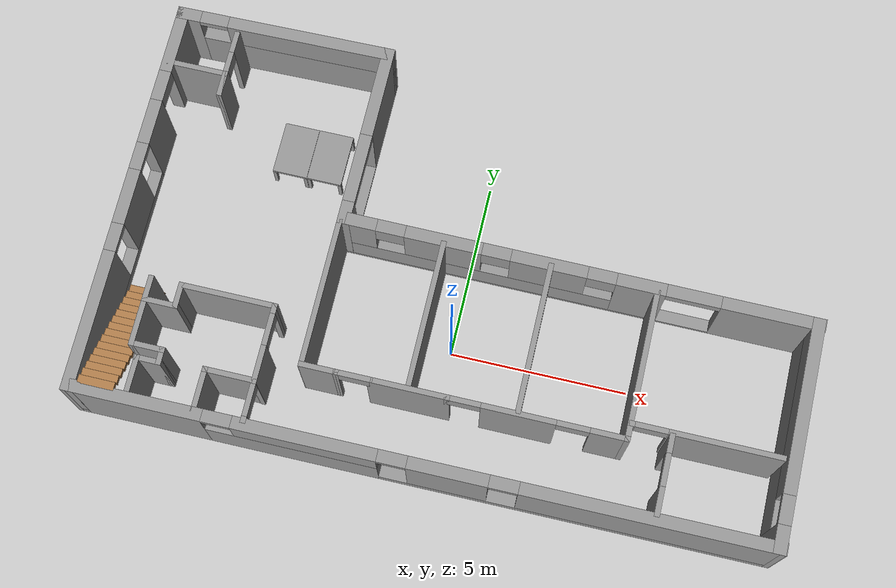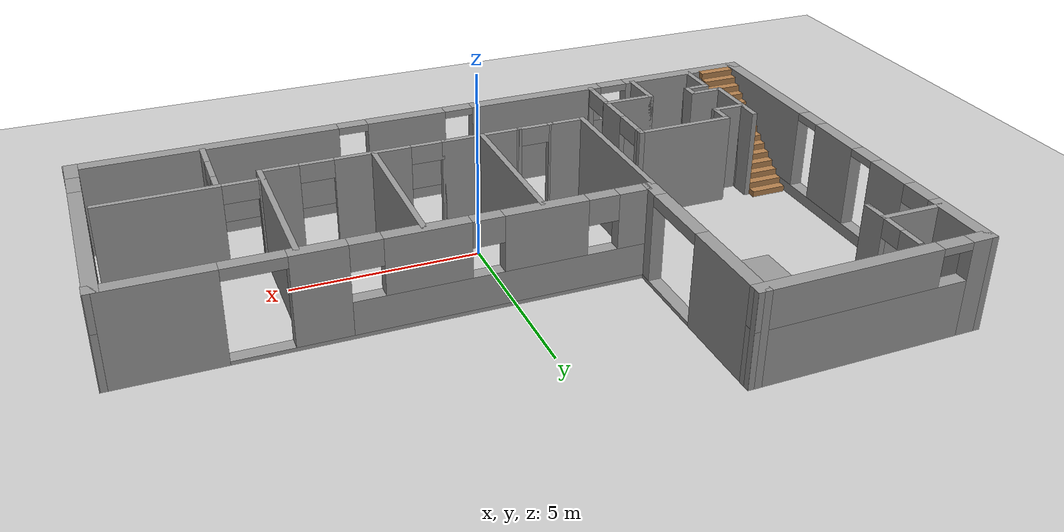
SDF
<sdf version="1.6">
 <world name="default">
  <plugin name="hello" filename="libhello.so"/>
  <light name="sun" type="directional">
   <pose>0 0 10 0 -0 0</pose>
   <diffuse>0.8 0.8 0.8 1</diffuse>
   <specular>0.2 0.2 0.2 1</specular>
   <attenuation>
    <range>1000</range>
    <constant>0.9</constant>
    <linear>0.01</linear>
    <quadratic>0.001</quadratic>
   </attenuation>
   <direction>-0.5 0.1 -0.9</direction>
  </light>
  <model name="ground_plane">
   <static>1</static>
   <link name="link">
    <collision name="collision">
     <geometry><plane><normal>0 0 1</normal><size>100 100</size></plane></geometry>
     <surface><friction><ode><mu>100</mu><mu2>50</mu2></ode></friction></surface>
    </collision>
    <visual name="visual">
     <cast_shadows>0</cast_shadows>
     <geometry><plane><normal>0 0 1</normal><size>100 100</size></plane></geometry>
     <material>
      <script><uri>file://media/materials/scripts/gazebo.material</uri><name>Gazebo/Grey</name></script>
     </material>
    </visual>
   </link>
  </model>
  <gravity>0 0 -9.8</gravity>
  <magnetic_field>6e-06 2.3e-05 -4.2e-05</magnetic_field>
  <atmosphere type="adiabatic"/>
  <physics name="default_physics" default="0" type="ode">
   <max_step_size>0.001</max_step_size>
   <real_time_factor>1</real_time_factor>
   <real_time_update_rate>1000</real_time_update_rate>
  </physics>
  <scene><ambient>0.4 0.4 0.4 1</ambient><background>0.7 0.7 0.7 1</background><shadows>1</shadows></scene>
  <spherical_coordinates>
   <surface_model>EARTH_WGS84</surface_model>
   <latitude_deg>0</latitude_deg>
   <longitude_deg>0</longitude_deg>
   <elevation>0</elevation>
   <heading_deg>0</heading_deg>
  </spherical_coordinates>
  <model name="home">
   <pose>-0.006982 1.84803 0 0 -0 0</pose>
   <link name="Stairs_0">
    <visual name="Stairs_0_Visual_0">
     <pose>-8.81629 -2.10282 0.083333 0 -0 0</pose>
     <geometry><box><size>1 0.233333 0.166667</size></box></geometry>
     <material>
      <script><uri>file://media/materials/scripts/gazebo.material</uri><name>Gazebo/Wood</name></script>
      <ambient>1 1 1 1</ambient>
     </material>
     <meta><layer>0</layer></meta>
    </visual>
    <collision name="Stairs_0_Collision_0">
     <geometry><box><size>1 0.233333 0.166667</size></box></geometry>
     <pose>-8.81629 -2.10282 0.083333 0 -0 0</pose>
    </collision>
    <visual name="Stairs_0_Visual_1">
     <pose>-8.81629 -2.33615 0.25 0 -0 0</pose>
     <geometry><box><size>1 0.233333 0.166667</size></box></geometry>
     <material>
      <script><uri>file://media/materials/scripts/gazebo.material</uri><name>Gazebo/Wood</name></script>
      <ambient>1 1 1 1</ambient>
     </material>
     <meta><layer>0</layer></meta>
    </visual>
    <collision name="Stairs_0_Collision_1">
     <geometry><box><size>1 0.233333 0.166667</size></box></geometry>
     <pose>-8.81629 -2.33615 0.25 0 -0 0</pose>
    </collision>
    <visual name="Stairs_0_Visual_2">
     <pose>-8.81629 -2.56948 0.416667 0 -0 0</pose>
     <geometry><box><size>1 0.233333 0.166667</size></box></geometry>
     <material>
      <script><uri>file://media/materials/scripts/gazebo.material</uri><name>Gazebo/Wood</name></script>
      <ambient>1 1 1 1</ambient>
     </material>
     <meta><layer>0</layer></meta>
    </visual>
    <collision name="Stairs_0_Collision_2">
     <geometry><box><size>1 0.233333 0.166667</size></box></geometry>
     <pose>-8.81629 -2.56948 0.416667 0 -0 0</pose>
    </collision>
    <visual name="Stairs_0_Visual_3">
     <pose>-8.81629 -2.80282 0.583333 0 -0 0</pose>
     <geometry><box><size>1 0.233333 0.166667</size></box></geometry>
     <material>
      <script><uri>file://media/materials/scripts/gazebo.material</uri><name>Gazebo/Wood</name></script>
      <ambient>1 1 1 1</ambient>
     </material>
     <meta><layer>0</layer></meta>
    </visual>
    <collision name="Stairs_0_Collision_3">
     <geometry><box><size>1 0.233333 0.166667</size></box></geometry>
     <pose>-8.81629 -2.80282 0.583333 0 -0 0</pose>
    </collision>
    <visual name="Stairs_0_Visual_4">
     <pose>-8.81629 -3.03615 0.75 0 -0 0</pose>
     <geometry><box><size>1 0.233333 0.166667</size></box></geometry>
     <material>
      <script><uri>file://media/materials/scripts/gazebo.material</uri><name>Gazebo/Wood</name></script>
      <ambient>1 1 1 1</ambient>
     </material>
     <meta><layer>0</layer></meta>
    </visual>
    <collision name="Stairs_0_Collision_4">
     <geometry><box><size>1 0.233333 0.166667</size></box></geometry>
     <pose>-8.81629 -3.03615 0.75 0 -0 0</pose>
    </collision>
    <visual name="Stairs_0_Visual_5">
     <pose>-8.81629 -3.26948 0.916667 0 -0 0</pose>
     <geometry><box><size>1 0.233333 0.166667</size></box></geometry>
     <material>
      <script><uri>file://media/materials/scripts/gazebo.material</uri><name>Gazebo/Wood</name></script>
      <ambient>1 1 1 1</ambient>
     </material>
     <meta><layer>0</layer></meta>
    </visual>
    <collision name="Stairs_0_Collision_5">
     <geometry><box><size>1 0.233333 0.166667</size></box></geometry>
     <pose>-8.81629 -3.26948 0.916667 0 -0 0</pose>
    </collision>
    <visual name="Stairs_0_Visual_6">
     <pose>-8.81629 -3.50282 1.08333 0 -0 0</pose>
     <geometry><box><size>1 0.233333 0.166667</size></box></geometry>
     <material>
      <script><uri>file://media/materials/scripts/gazebo.material</uri><name>Gazebo/Wood</name></script>
      <ambient>1 1 1 1</ambient>
     </material>
     <meta><layer>0</layer></meta>
    </visual>
    <collision name="Stairs_0_Collision_6">
     <geometry><box><size>1 0.233333 0.166667</size></box></geometry>
     <pose>-8.81629 -3.50282 1.08333 0 -0 0</pose>
    </collision>
    <visual name="Stairs_0_Visual_7">
     <pose>-8.81629 -3.73615 1.25 0 -0 0</pose>
     <geometry><box><size>1 0.233333 0.166667</size></box></geometry>
     <material>
      <script><uri>file://media/materials/scripts/gazebo.material</uri><name>Gazebo/Wood</name></script>
      <ambient>1 1 1 1</ambient>
     </material>
     <meta><layer>0</layer></meta>
    </visual>
    <collision name="Stairs_0_Collision_7">
     <geometry><box><size>1 0.233333 0.166667</size></box></geometry>
     <pose>-8.81629 -3.73615 1.25 0 -0 0</pose>
    </collision>
    <visual name="Stairs_0_Visual_8">
     <pose>-8.81629 -3.96949 1.41667 0 -0 0</pose>
     <geometry><box><size>1 0.233333 0.166667</size></box></geometry>
     <material>
      <script><uri>file://media/materials/scripts/gazebo.material</uri><name>Gazebo/Wood</name></script>
      <ambient>1 1 1 1</ambient>
     </material>
     <meta><layer>0</layer></meta>
    </visual>
    <collision name="Stairs_0_Collision_8">
     <geometry><box><size>1 0.233333 0.166667</size></box></geometry>
     <pose>-8.81629 -3.96949 1.41667 0 -0 0</pose>
    </collision>
    <visual name="Stairs_0_Visual_9">
     <pose>-8.81629 -4.20282 1.58333 0 -0 0</pose>
     <geometry><box><size>1 0.233333 0.166667</size></box></geometry>
     <material>
      <script><uri>file://media/materials/scripts/gazebo.material</uri><name>Gazebo/Wood</name></script>
      <ambient>1 1 1 1</ambient>
     </material>
     <meta><layer>0</layer></meta>
    </visual>
    <collision name="Stairs_0_Collision_9">
     <geometry><box><size>1 0.233333 0.166667</size></box></geometry>
     <pose>-8.81629 -4.20282 1.58333 0 -0 0</pose>
    </collision>
    <visual name="Stairs_0_Visual_10">
     <pose>-8.81629 -4.43615 1.75 0 -0 0</pose>
     <geometry><box><size>1 0.233333 0.166667</size></box></geometry>
     <material>
      <script><uri>file://media/materials/scripts/gazebo.material</uri><name>Gazebo/Wood</name></script>
      <ambient>1 1 1 1</ambient>
     </material>
     <meta><layer>0</layer></meta>
    </visual>
    <collision name="Stairs_0_Collision_10">
     <geometry><box><size>1 0.233333 0.166667</size></box></geometry>
     <pose>-8.81629 -4.43615 1.75 0 -0 0</pose>
    </collision>
    <visual name="Stairs_0_Visual_11">
     <pose>-8.81629 -4.66948 1.91667 0 -0 0</pose>
     <geometry><box><size>1 0.233333 0.166667</size></box></geometry>
     <material>
      <script><uri>file://media/materials/scripts/gazebo.material</uri><name>Gazebo/Wood</name></script>
      <ambient>1 1 1 1</ambient>
     </material>
     <meta><layer>0</layer></meta>
    </visual>
    <collision name="Stairs_0_Collision_11">
     <geometry><box><size>1 0.233333 0.166667</size></box></geometry>
     <pose>-8.81629 -4.66948 1.91667 0 -0 0</pose>
    </collision>
    <visual name="Stairs_0_Visual_12">
     <pose>-8.81629 -4.90282 2.08333 0 -0 0</pose>
     <geometry><box><size>1 0.233333 0.166667</size></box></geometry>
     <material>
      <script><uri>file://media/materials/scripts/gazebo.material</uri><name>Gazebo/Wood</name></script>
      <ambient>1 1 1 1</ambient>
     </material>
     <meta><layer>0</layer></meta>
    </visual>
    <collision name="Stairs_0_Collision_12">
     <geometry><box><size>1 0.233333 0.166667</size></box></geometry>
     <pose>-8.81629 -4.90282 2.08333 0 -0 0</pose>
    </collision>
    <visual name="Stairs_0_Visual_13">
     <pose>-8.81629 -5.13615 2.25 0 -0 0</pose>
     <geometry><box><size>1 0.233333 0.166667</size></box></geometry>
     <material>
      <script><uri>file://media/materials/scripts/gazebo.material</uri><name>Gazebo/Wood</name></script>
      <ambient>1 1 1 1</ambient>
     </material>
     <meta><layer>0</layer></meta>
    </visual>
    <collision name="Stairs_0_Collision_13">
     <geometry><box><size>1 0.233333 0.166667</size></box></geometry>
     <pose>-8.81629 -5.13615 2.25 0 -0 0</pose>
    </collision>
    <visual name="Stairs_0_Visual_14">
     <pose>-8.81629 -5.36949 2.41667 0 -0 0</pose>
     <geometry><box><size>1 0.233333 0.166667</size></box></geometry>
     <material>
      <script><uri>file://media/materials/scripts/gazebo.material</uri><name>Gazebo/Wood</name></script>
      <ambient>1 1 1 1</ambient>
     </material>
     <meta><layer>0</layer></meta>
    </visual>
    <collision name="Stairs_0_Collision_14">
     <geometry><box><size>1 0.233333 0.166667</size></box></geometry>
     <pose>-8.81629 -5.36949 2.41667 0 -0 0</pose>
    </collision>
   </link>
   <link name="Wall_0">
    <pose>-9.53364 -0.044972 0 0 0 -1.5708</pose>
    <visual name="Wall_0_Visual_0">
     <pose>-4.71962 0 1.25 0 -0 0</pose>
     <geometry><box><size>2.01097 0.35 2.5</size></box></geometry>
     <material>
      <script><uri>file://media/materials/scripts/gazebo.material</uri><name>Gazebo/Grey</name></script>
      <ambient>0.533333 0.541176 0.521569 1</ambient>
     </material>
     <meta><layer>0</layer></meta>
    </visual>
    <collision name="Wall_0_Collision_0">
     <geometry><box><size>2.01097 0.35 2.5</size></box></geometry>
     <pose>-4.71962 0 1.25 0 -0 0</pose>
    </collision>
    <visual name="Wall_0_Visual_1">
     <pose>-2.15318 0 1.25 0 -0 0</pose>
     <geometry><box><size>1.32191 0.35 2.5</size></box></geometry>
     <material>
      <script><uri>file://media/materials/scripts/gazebo.material</uri><name>Gazebo/Grey</name></script>
      <ambient>0.533333 0.541176 0.521569 1</ambient>
     </material>
     <meta><layer>0</layer></meta>
    </visual>
    <collision name="Wall_0_Collision_1">
     <geometry><box><size>1.32191 0.35 2.5</size></box></geometry>
     <pose>-2.15318 0 1.25 0 -0 0</pose>
    </collision>
    <visual name="Wall_0_Visual_2">
     <pose>2.11644 0 0.15 0 -0 0</pose>
     <geometry><box><size>7.21733 0.35 0.3</size></box></geometry>
     <material>
      <script><uri>file://media/materials/scripts/gazebo.material</uri><name>Gazebo/Grey</name></script>
      <ambient>0.533333 0.541176 0.521569 1</ambient>
     </material>
     <meta><layer>0</layer></meta>
    </visual>
    <collision name="Wall_0_Collision_2">
     <geometry><box><size>7.21733 0.35 0.3</size></box></geometry>
     <pose>2.11644 0 0.15 0 -0 0</pose>
    </collision>
    <visual name="Wall_0_Visual_3">
     <pose>0.116089 0 1.4 0 -0 0</pose>
     <geometry><box><size>1.61663 0.35 2.2</size></box></geometry>
     <material>
      <script><uri>file://media/materials/scripts/gazebo.material</uri><name>Gazebo/Grey</name></script>
      <ambient>0.533333 0.541176 0.521569 1</ambient>
     </material>
     <meta><layer>0</layer></meta>
    </visual>
    <collision name="Wall_0_Collision_3">
     <geometry><box><size>1.61663 0.35 2.2</size></box></geometry>
     <pose>0.116089 0 1.4 0 -0 0</pose>
    </collision>
    <visual name="Wall_0_Visual_4">
     <pose>3.72475 0 1.4 0 -0 0</pose>
     <geometry><box><size>4.0007 0.35 2.2</size></box></geometry>
     <material>
      <script><uri>file://media/materials/scripts/gazebo.material</uri><name>Gazebo/Grey</name></script>
      <ambient>0.533333 0.541176 0.521569 1</ambient>
     </material>
     <meta><layer>0</layer></meta>
    </visual>
    <collision name="Wall_0_Collision_4">
     <geometry><box><size>4.0007 0.35 2.2</size></box></geometry>
     <pose>3.72475 0 1.4 0 -0 0</pose>
    </collision>
    <visual name="Wall_0_Visual_5">
     <pose>-3.26413 0 2.25 0 -0 0</pose>
     <geometry><box><size>0.9 0.35 0.5</size></box></geometry>
     <material>
      <script><uri>file://media/materials/scripts/gazebo.material</uri><name>Gazebo/Grey</name></script>
      <ambient>0.533333 0.541176 0.521569 1</ambient>
     </material>
     <meta><layer>0</layer></meta>
    </visual>
    <collision name="Wall_0_Collision_5">
     <geometry><box><size>0.9 0.35 0.5</size></box></geometry>
     <pose>-3.26413 0 2.25 0 -0 0</pose>
    </collision>
    <visual name="Wall_0_Visual_6">
     <pose>-1.09223 0 2.4 0 -0 0</pose>
     <geometry><box><size>0.8 0.35 0.2</size></box></geometry>
     <material>
      <script><uri>file://media/materials/scripts/gazebo.material</uri><name>Gazebo/Grey</name></script>
      <ambient>0.533333 0.541176 0.521569 1</ambient>
     </material>
     <meta><layer>0</layer></meta>
    </visual>
    <collision name="Wall_0_Collision_6">
     <geometry><box><size>0.8 0.35 0.2</size></box></geometry>
     <pose>-1.09223 0 2.4 0 -0 0</pose>
    </collision>
    <visual name="Wall_0_Visual_7">
     <pose>1.3244 0 2.4 0 -0 0</pose>
     <geometry><box><size>0.8 0.35 0.2</size></box></geometry>
     <material>
      <script><uri>file://media/materials/scripts/gazebo.material</uri><name>Gazebo/Grey</name></script>
      <ambient>0.533333 0.541176 0.521569 1</ambient>
     </material>
     <meta><layer>0</layer></meta>
    </visual>
    <collision name="Wall_0_Collision_7">
     <geometry><box><size>0.8 0.35 0.2</size></box></geometry>
     <pose>1.3244 0 2.4 0 -0 0</pose>
    </collision>
   </link>
   <link name="Wall_1">
    <pose>0.000972 -5.56103 0 0 -0 0.00356</pose>
    <visual name="Wall_1_Visual_0">
     <pose>-7.79255 0 1.25 0 -0 0</pose>
     <geometry><box><size>3.83426 0.35 2.5</size></box></geometry>
     <material>
      <script><uri>file://media/materials/scripts/gazebo.material</uri><name>Gazebo/Grey</name></script>
      <ambient>0.533333 0.541176 0.521569 1</ambient>
     </material>
     <meta><layer>0</layer></meta>
    </visual>
    <collision name="Wall_1_Collision_0">
     <geometry><box><size>3.83426 0.35 2.5</size></box></geometry>
     <pose>-7.79255 0 1.25 0 -0 0</pose>
    </collision>
    <visual name="Wall_1_Visual_1">
     <pose>-3.50442 0 0.75 0 -0 0</pose>
     <geometry><box><size>4.742 0.35 1.5</size></box></geometry>
     <material>
      <script><uri>file://media/materials/scripts/gazebo.material</uri><name>Gazebo/Grey</name></script>
      <ambient>0.533333 0.541176 0.521569 1</ambient>
     </material>
     <meta><layer>0</layer></meta>
    </visual>
    <collision name="Wall_1_Collision_1">
     <geometry><box><size>4.742 0.35 1.5</size></box></geometry>
     <pose>-3.50442 0 0.75 0 -0 0</pose>
    </collision>
    <visual name="Wall_1_Visual_2">
     <pose>4.28813 0 0.15 0 -0 0</pose>
     <geometry><box><size>10.8431 0.35 0.3</size></box></geometry>
     <material>
      <script><uri>file://media/materials/scripts/gazebo.material</uri><name>Gazebo/Grey</name></script>
      <ambient>0.533333 0.541176 0.521569 1</ambient>
     </material>
     <meta><layer>0</layer></meta>
    </visual>
    <collision name="Wall_1_Collision_2">
     <geometry><box><size>10.8431 0.35 0.3</size></box></geometry>
     <pose>4.28813 0 0.15 0 -0 0</pose>
    </collision>
    <visual name="Wall_1_Visual_3">
     <pose>0.765465 0 1.4 0 -0 0</pose>
     <geometry><box><size>2.19777 0.35 2.2</size></box></geometry>
     <material>
      <script><uri>file://media/materials/scripts/gazebo.material</uri><name>Gazebo/Grey</name></script>
      <ambient>0.533333 0.541176 0.521569 1</ambient>
     </material>
     <meta><layer>0</layer></meta>
    </visual>
    <collision name="Wall_1_Collision_3">
     <geometry><box><size>2.19777 0.35 2.2</size></box></geometry>
     <pose>0.765465 0 1.4 0 -0 0</pose>
    </collision>
    <visual name="Wall_1_Visual_4">
     <pose>6.18701 0 1.4 0 -0 0</pose>
     <geometry><box><size>7.04532 0.35 2.2</size></box></geometry>
     <material>
      <script><uri>file://media/materials/scripts/gazebo.material</uri><name>Gazebo/Grey</name></script>
      <ambient>0.533333 0.541176 0.521569 1</ambient>
     </material>
     <meta><layer>0</layer></meta>
    </visual>
    <collision name="Wall_1_Collision_4">
     <geometry><box><size>7.04532 0.35 2.2</size></box></geometry>
     <pose>6.18701 0 1.4 0 -0 0</pose>
    </collision>
    <visual name="Wall_1_Visual_5">
     <pose>-3.10442 0 2 0 -0 0</pose>
     <geometry><box><size>3.942 0.35 1</size></box></geometry>
     <material>
      <script><uri>file://media/materials/scripts/gazebo.material</uri><name>Gazebo/Grey</name></script>
      <ambient>0.533333 0.541176 0.521569 1</ambient>
     </material>
     <meta><layer>0</layer></meta>
    </visual>
    <collision name="Wall_1_Collision_5">
     <geometry><box><size>3.942 0.35 1</size></box></geometry>
     <pose>-3.10442 0 2 0 -0 0</pose>
    </collision>
    <visual name="Wall_1_Visual_6">
     <pose>-5.47542 0 2.4 0 -0 0</pose>
     <geometry><box><size>0.8 0.35 0.2</size></box></geometry>
     <material>
      <script><uri>file://media/materials/scripts/gazebo.material</uri><name>Gazebo/Grey</name></script>
      <ambient>0.533333 0.541176 0.521569 1</ambient>
     </material>
     <meta><layer>0</layer></meta>
    </visual>
    <collision name="Wall_1_Collision_6">
     <geometry><box><size>0.8 0.35 0.2</size></box></geometry>
     <pose>-5.47542 0 2.4 0 -0 0</pose>
    </collision>
    <visual name="Wall_1_Visual_7">
     <pose>2.26435 0 2.4 0 -0 0</pose>
     <geometry><box><size>0.8 0.35 0.2</size></box></geometry>
     <material>
      <script><uri>file://media/materials/scripts/gazebo.material</uri><name>Gazebo/Grey</name></script>
      <ambient>0.533333 0.541176 0.521569 1</ambient>
     </material>
     <meta><layer>0</layer></meta>
    </visual>
    <collision name="Wall_1_Collision_7">
     <geometry><box><size>0.8 0.35 0.2</size></box></geometry>
     <pose>2.26435 0 2.4 0 -0 0</pose>
    </collision>
    <visual name="Wall_1_Visual_8">
     <pose>-0.733419 0 2.4 0 -0 0</pose>
     <geometry><box><size>0.8 0.35 0.2</size></box></geometry>
     <material>
      <script><uri>file://media/materials/scripts/gazebo.material</uri><name>Gazebo/Grey</name></script>
      <ambient>0.533333 0.541176 0.521569 1</ambient>
     </material>
     <meta><layer>0</layer></meta>
    </visual>
    <collision name="Wall_1_Collision_8">
     <geometry><box><size>0.8 0.35 0.2</size></box></geometry>
     <pose>-0.733419 0 2.4 0 -0 0</pose>
    </collision>
   </link>
   <link name="Wall_17">
    <pose>-3.57864 3.09303 0 0 0 -1.5708</pose>
    <visual name="Wall_17_Visual_0">
     <pose>-1.33506 0 1.25 0 -0 0</pose>
     <geometry><box><size>2.68042 0.35 2.5</size></box></geometry>
     <material>
      <script><uri>file://media/materials/scripts/gazebo.material</uri><name>Gazebo/Grey</name></script>
      <ambient>0.533333 0.541176 0.521569 1</ambient>
     </material>
     <meta><layer>0</layer></meta>
    </visual>
    <collision name="Wall_17_Collision_0">
     <geometry><box><size>2.68042 0.35 2.5</size></box></geometry>
     <pose>-1.33506 0 1.25 0 -0 0</pose>
    </collision>
    <visual name="Wall_17_Visual_1">
     <pose>1.34021 0 0.05 0 -0 0</pose>
     <geometry><box><size>2.67013 0.35 0.1</size></box></geometry>
     <material>
      <script><uri>file://media/materials/scripts/gazebo.material</uri><name>Gazebo/Grey</name></script>
      <ambient>0.533333 0.541176 0.521569 1</ambient>
     </material>
     <meta><layer>0</layer></meta>
    </visual>
    <collision name="Wall_17_Collision_1">
     <geometry><box><size>2.67013 0.35 0.1</size></box></geometry>
     <pose>1.34021 0 0.05 0 -0 0</pose>
    </collision>
    <visual name="Wall_17_Visual_2">
     <pose>2.34021 0 1.3 0 -0 0</pose>
     <geometry><box><size>0.670125 0.35 2.4</size></box></geometry>
     <material>
      <script><uri>file://media/materials/scripts/gazebo.material</uri><name>Gazebo/Grey</name></script>
      <ambient>0.533333 0.541176 0.521569 1</ambient>
     </material>
     <meta><layer>0</layer></meta>
    </visual>
    <collision name="Wall_17_Collision_2">
     <geometry><box><size>0.670125 0.35 2.4</size></box></geometry>
     <pose>2.34021 0 1.3 0 -0 0</pose>
    </collision>
    <visual name="Wall_17_Visual_3">
     <pose>1.00515 0 2.35 0 -0 0</pose>
     <geometry><box><size>2 0.35 0.3</size></box></geometry>
     <material>
      <script><uri>file://media/materials/scripts/gazebo.material</uri><name>Gazebo/Grey</name></script>
      <ambient>0.533333 0.541176 0.521569 1</ambient>
     </material>
     <meta><layer>0</layer></meta>
    </visual>
    <collision name="Wall_17_Collision_3">
     <geometry><box><size>2 0.35 0.3</size></box></geometry>
     <pose>1.00515 0 2.35 0 -0 0</pose>
    </collision>
   </link>
   <link name="Wall_2">
    <pose>9.51547 -2.47709 0 0 -0 1.5708</pose>
    <visual name="Wall_2_Visual_0">
     <pose>-2.83404 0 1.25 0 -0 0</pose>
     <geometry><box><size>0.781917 0.35 2.5</size></box></geometry>
     <material>
      <script><uri>file://media/materials/scripts/gazebo.material</uri><name>Gazebo/Grey</name></script>
      <ambient>0.533333 0.541176 0.521569 1</ambient>
     </material>
     <meta><layer>0</layer></meta>
    </visual>
    <collision name="Wall_2_Collision_0">
     <geometry><box><size>0.781917 0.35 2.5</size></box></geometry>
     <pose>-2.83404 0 1.25 0 -0 0</pose>
    </collision>
    <visual name="Wall_2_Visual_1">
     <pose>0.390958 0 0.75 0 -0 0</pose>
     <geometry><box><size>5.66808 0.35 1.5</size></box></geometry>
     <material>
      <script><uri>file://media/materials/scripts/gazebo.material</uri><name>Gazebo/Grey</name></script>
      <ambient>0.533333 0.541176 0.521569 1</ambient>
     </material>
     <meta><layer>0</layer></meta>
    </visual>
    <collision name="Wall_2_Collision_1">
     <geometry><box><size>5.66808 0.35 1.5</size></box></geometry>
     <pose>0.390958 0 0.75 0 -0 0</pose>
    </collision>
    <visual name="Wall_2_Visual_2">
     <pose>0.790958 0 2 0 -0 0</pose>
     <geometry><box><size>4.86808 0.35 1</size></box></geometry>
     <material>
      <script><uri>file://media/materials/scripts/gazebo.material</uri><name>Gazebo/Grey</name></script>
      <ambient>0.533333 0.541176 0.521569 1</ambient>
     </material>
     <meta><layer>0</layer></meta>
    </visual>
    <collision name="Wall_2_Collision_2">
     <geometry><box><size>4.86808 0.35 1</size></box></geometry>
     <pose>0.790958 0 2 0 -0 0</pose>
    </collision>
    <visual name="Wall_2_Visual_3">
     <pose>-2.04308 0 2.4 0 -0 0</pose>
     <geometry><box><size>0.8 0.35 0.2</size></box></geometry>
     <material>
      <script><uri>file://media/materials/scripts/gazebo.material</uri><name>Gazebo/Grey</name></script>
      <ambient>0.533333 0.541176 0.521569 1</ambient>
     </material>
     <meta><layer>0</layer></meta>
    </visual>
    <collision name="Wall_2_Collision_3">
     <geometry><box><size>0.8 0.35 0.2</size></box></geometry>
     <pose>-2.04308 0 2.4 0 -0 0</pose>
    </collision>
   </link>
   <link name="Wall_24">
    <collision name="Wall_24_Collision">
     <geometry><box><size>4.25 0.15 2.5</size></box></geometry>
     <pose>0 0 1.25 0 -0 0</pose>
    </collision>
    <visual name="Wall_24_Visual">
     <pose>0 0 1.25 0 -0 0</pose>
     <geometry><box><size>4.25 0.15 2.5</size></box></geometry>
     <material>
      <script><uri>file://media/materials/scripts/gazebo.material</uri><name>Gazebo/Grey</name></script>
      <ambient>1 1 1 1</ambient>
     </material>
     <meta><layer>0</layer></meta>
    </visual>
    <pose>-3.67864 -1.59397 0 0 -0 1.5708</pose>
   </link>
   <link name="Wall_26">
    <collision name="Wall_26_Collision">
     <geometry><box><size>1.1 0.15 2.5</size></box></geometry>
     <pose>0 0 1.25 0 -0 0</pose>
    </collision>
    <visual name="Wall_26_Visual">
     <pose>0 0 1.25 0 -0 0</pose>
     <geometry><box><size>1.1 0.15 2.5</size></box></geometry>
     <material>
      <script><uri>file://media/materials/scripts/gazebo.material</uri><name>Gazebo/Grey</name></script>
      <ambient>1 1 1 1</ambient>
     </material>
     <meta><layer>0</layer></meta>
    </visual>
    <pose>-3.20364 -3.64397 0 0 -0 0</pose>
   </link>
   <link name="Wall_3">
    <pose>3.09047 0.582971 0 0 -0 3.14003</pose>
    <visual name="Wall_3_Visual_0">
     <pose>-5.20519 0 1.25 0 -0 0</pose>
     <geometry><box><size>2.82987 0.35 2.5</size></box></geometry>
     <material>
      <script><uri>file://media/materials/scripts/gazebo.material</uri><name>Gazebo/Grey</name></script>
      <ambient>0.533333 0.541176 0.521569 1</ambient>
     </material>
     <meta><layer>0</layer></meta>
    </visual>
    <collision name="Wall_3_Collision_0">
     <geometry><box><size>2.82987 0.35 2.5</size></box></geometry>
     <pose>-5.20519 0 1.25 0 -0 0</pose>
    </collision>
    <visual name="Wall_3_Visual_1">
     <pose>1.41494 0 0.05 0 -0 0</pose>
     <geometry><box><size>10.4104 0.35 0.1</size></box></geometry>
     <material>
      <script><uri>file://media/materials/scripts/gazebo.material</uri><name>Gazebo/Grey</name></script>
      <ambient>0.533333 0.541176 0.521569 1</ambient>
     </material>
     <meta><layer>0</layer></meta>
    </visual>
    <collision name="Wall_3_Collision_1">
     <geometry><box><size>10.4104 0.35 0.1</size></box></geometry>
     <pose>1.41494 0 0.05 0 -0 0</pose>
    </collision>
    <visual name="Wall_3_Visual_2">
     <pose>-1.60539 0 1.3 0 -0 0</pose>
     <geometry><box><size>1.36971 0.35 2.4</size></box></geometry>
     <material>
      <script><uri>file://media/materials/scripts/gazebo.material</uri><name>Gazebo/Grey</name></script>
      <ambient>0.533333 0.541176 0.521569 1</ambient>
     </material>
     <meta><layer>0</layer></meta>
    </visual>
    <collision name="Wall_3_Collision_2">
     <geometry><box><size>1.36971 0.35 2.4</size></box></geometry>
     <pose>-1.60539 0 1.3 0 -0 0</pose>
    </collision>
    <visual name="Wall_3_Visual_3">
     <pose>2.84979 0 0.55 0 -0 0</pose>
     <geometry><box><size>7.54066 0.35 0.9</size></box></geometry>
     <material>
      <script><uri>file://media/materials/scripts/gazebo.material</uri><name>Gazebo/Grey</name></script>
      <ambient>0.533333 0.541176 0.521569 1</ambient>
     </material>
     <meta><layer>0</layer></meta>
    </visual>
    <collision name="Wall_3_Collision_3">
     <geometry><box><size>7.54066 0.35 0.9</size></box></geometry>
     <pose>2.84979 0 0.55 0 -0 0</pose>
    </collision>
    <visual name="Wall_3_Visual_4">
     <pose>0.940109 0 1.75 0 -0 0</pose>
     <geometry><box><size>2.12129 0.35 1.5</size></box></geometry>
     <material>
      <script><uri>file://media/materials/scripts/gazebo.material</uri><name>Gazebo/Grey</name></script>
      <ambient>0.533333 0.541176 0.521569 1</ambient>
     </material>
     <meta><layer>0</layer></meta>
    </visual>
    <collision name="Wall_3_Collision_4">
     <geometry><box><size>2.12129 0.35 1.5</size></box></geometry>
     <pose>0.940109 0 1.75 0 -0 0</pose>
    </collision>
    <visual name="Wall_3_Visual_5">
     <pose>3.87689 0 1.75 0 -0 0</pose>
     <geometry><box><size>2.15226 0.35 1.5</size></box></geometry>
     <material>
      <script><uri>file://media/materials/scripts/gazebo.material</uri><name>Gazebo/Grey</name></script>
      <ambient>0.533333 0.541176 0.521569 1</ambient>
     </material>
     <meta><layer>0</layer></meta>
    </visual>
    <collision name="Wall_3_Collision_5">
     <geometry><box><size>2.15226 0.35 1.5</size></box></geometry>
     <pose>3.87689 0 1.75 0 -0 0</pose>
    </collision>
    <visual name="Wall_3_Visual_6">
     <pose>6.18657 0 1.75 0 -0 0</pose>
     <geometry><box><size>0.867103 0.35 1.5</size></box></geometry>
     <material>
      <script><uri>file://media/materials/scripts/gazebo.material</uri><name>Gazebo/Grey</name></script>
      <ambient>0.533333 0.541176 0.521569 1</ambient>
     </material>
     <meta><layer>0</layer></meta>
    </visual>
    <collision name="Wall_3_Collision_6">
     <geometry><box><size>0.867103 0.35 1.5</size></box></geometry>
     <pose>6.18657 0 1.75 0 -0 0</pose>
    </collision>
    <visual name="Wall_3_Visual_7">
     <pose>-0.520537 0 2.15 0 -0 0</pose>
     <geometry><box><size>0.8 0.35 0.7</size></box></geometry>
     <material>
      <script><uri>file://media/materials/scripts/gazebo.material</uri><name>Gazebo/Grey</name></script>
      <ambient>0.533333 0.541176 0.521569 1</ambient>
     </material>
     <meta><layer>0</layer></meta>
    </visual>
    <collision name="Wall_3_Collision_7">
     <geometry><box><size>0.8 0.35 0.7</size></box></geometry>
     <pose>-0.520537 0 2.15 0 -0 0</pose>
    </collision>
    <visual name="Wall_3_Visual_8">
     <pose>2.40076 0 2.15 0 -0 0</pose>
     <geometry><box><size>0.8 0.35 0.7</size></box></geometry>
     <material>
      <script><uri>file://media/materials/scripts/gazebo.material</uri><name>Gazebo/Grey</name></script>
      <ambient>0.533333 0.541176 0.521569 1</ambient>
     </material>
     <meta><layer>0</layer></meta>
    </visual>
    <collision name="Wall_3_Collision_8">
     <geometry><box><size>0.8 0.35 0.7</size></box></geometry>
     <pose>2.40076 0 2.15 0 -0 0</pose>
    </collision>
    <visual name="Wall_3_Visual_9">
     <pose>5.35302 0 2.15 0 -0 0</pose>
     <geometry><box><size>0.8 0.35 0.7</size></box></geometry>
     <material>
      <script><uri>file://media/materials/scripts/gazebo.material</uri><name>Gazebo/Grey</name></script>
      <ambient>0.533333 0.541176 0.521569 1</ambient>
     </material>
     <meta><layer>0</layer></meta>
    </visual>
    <collision name="Wall_3_Collision_9">
     <geometry><box><size>0.8 0.35 0.7</size></box></geometry>
     <pose>5.35302 0 2.15 0 -0 0</pose>
    </collision>
    <visual name="Wall_3_Visual_10">
     <pose>-3.04025 0 2.35 0 -0 0</pose>
     <geometry><box><size>1.5 0.35 0.3</size></box></geometry>
     <material>
      <script><uri>file://media/materials/scripts/gazebo.material</uri><name>Gazebo/Grey</name></script>
      <ambient>0.533333 0.541176 0.521569 1</ambient>
     </material>
     <meta><layer>0</layer></meta>
    </visual>
    <collision name="Wall_3_Collision_10">
     <geometry><box><size>1.5 0.35 0.3</size></box></geometry>
     <pose>-3.04025 0 2.35 0 -0 0</pose>
    </collision>
   </link>
   <link name="Wall_30">
    <collision name="Wall_30_Collision">
     <geometry><box><size>2.25 0.15 2.5</size></box></geometry>
     <pose>0 0 1.25 0 -0 0</pose>
    </collision>
    <visual name="Wall_30_Visual">
     <pose>0 0 1.25 0 -0 0</pose>
     <geometry><box><size>2.25 0.15 2.5</size></box></geometry>
     <material>
      <script><uri>file://media/materials/scripts/gazebo.material</uri><name>Gazebo/Grey</name></script>
      <ambient>1 1 1 1</ambient>
     </material>
     <meta><layer>0</layer></meta>
    </visual>
    <pose>-0.756595 -3.64068 0 0 -0 0</pose>
   </link>
   <link name="Wall_32">
    <pose>-2.26762 -3.64233 0 0 -0 0.003569</pose>
    <visual name="Wall_32_Visual_0">
     <pose>-0.470675 0 1.25 0 -0 0</pose>
     <geometry><box><size>0.130703 0.15 2.5</size></box></geometry>
     <material>
      <script><uri>file://media/materials/scripts/gazebo.material</uri><name>Gazebo/Grey</name></script>
      <ambient>1 1 1 1</ambient>
     </material>
     <meta><layer>0</layer></meta>
    </visual>
    <collision name="Wall_32_Collision_0">
     <geometry><box><size>0.130703 0.15 2.5</size></box></geometry>
     <pose>-0.470675 0 1.25 0 -0 0</pose>
    </collision>
    <visual name="Wall_32_Visual_1">
     <pose>0.511319 0 1.25 0 -0 0</pose>
     <geometry><box><size>0.049415 0.15 2.5</size></box></geometry>
     <material>
      <script><uri>file://media/materials/scripts/gazebo.material</uri><name>Gazebo/Grey</name></script>
      <ambient>1 1 1 1</ambient>
     </material>
     <meta><layer>0</layer></meta>
    </visual>
    <collision name="Wall_32_Collision_1">
     <geometry><box><size>0.049415 0.15 2.5</size></box></geometry>
     <pose>0.511319 0 1.25 0 -0 0</pose>
    </collision>
    <visual name="Wall_32_Visual_2">
     <pose>0.040644 0 2.25 0 -0 0</pose>
     <geometry><box><size>0.891935 0.15 0.5</size></box></geometry>
     <material>
      <script><uri>file://media/materials/scripts/gazebo.material</uri><name>Gazebo/Grey</name></script>
      <ambient>1 1 1 1</ambient>
     </material>
     <meta><layer>0</layer></meta>
    </visual>
    <collision name="Wall_32_Collision_2">
     <geometry><box><size>0.891935 0.15 0.5</size></box></geometry>
     <pose>0.040644 0 2.25 0 -0 0</pose>
    </collision>
   </link>
   <link name="Wall_36">
    <collision name="Wall_36_Collision">
     <geometry><box><size>4.25 0.15 2.5</size></box></geometry>
     <pose>0 0 1.25 0 -0 0</pose>
    </collision>
    <visual name="Wall_36_Visual">
     <pose>0 0 1.25 0 -0 0</pose>
     <geometry><box><size>4.25 0.15 2.5</size></box></geometry>
     <material>
      <script><uri>file://media/materials/scripts/gazebo.material</uri><name>Gazebo/Grey</name></script>
      <ambient>1 1 1 1</ambient>
     </material>
     <meta><layer>0</layer></meta>
    </visual>
    <pose>-0.77097 -1.56098 0 0 -0 1.5708</pose>
   </link>
   <link name="Wall_38">
    <pose>2.71841 -3.64068 0 0 -0 0</pose>
    <visual name="Wall_38_Visual_0">
     <pose>-2.45469 0 1.25 0 -0 0</pose>
     <geometry><box><size>0.090625 0.15 2.5</size></box></geometry>
     <material>
      <script><uri>file://media/materials/scripts/gazebo.material</uri><name>Gazebo/Grey</name></script>
      <ambient>1 1 1 1</ambient>
     </material>
     <meta><layer>0</layer></meta>
    </visual>
    <collision name="Wall_38_Collision_0">
     <geometry><box><size>0.090625 0.15 2.5</size></box></geometry>
     <pose>-2.45469 0 1.25 0 -0 0</pose>
    </collision>
    <visual name="Wall_38_Visual_1">
     <pose>-0.489375 0 1.25 0 -0 0</pose>
     <geometry><box><size>2.04 0.15 2.5</size></box></geometry>
     <material>
      <script><uri>file://media/materials/scripts/gazebo.material</uri><name>Gazebo/Grey</name></script>
      <ambient>1 1 1 1</ambient>
     </material>
     <meta><layer>0</layer></meta>
    </visual>
    <collision name="Wall_38_Collision_1">
     <geometry><box><size>2.04 0.15 2.5</size></box></geometry>
     <pose>-0.489375 0 1.25 0 -0 0</pose>
    </collision>
    <visual name="Wall_38_Visual_2">
     <pose>1.96531 0 1.25 0 -0 0</pose>
     <geometry><box><size>1.06937 0.15 2.5</size></box></geometry>
     <material>
      <script><uri>file://media/materials/scripts/gazebo.material</uri><name>Gazebo/Grey</name></script>
      <ambient>1 1 1 1</ambient>
     </material>
     <meta><layer>0</layer></meta>
    </visual>
    <collision name="Wall_38_Collision_2">
     <geometry><box><size>1.06937 0.15 2.5</size></box></geometry>
     <pose>1.96531 0 1.25 0 -0 0</pose>
    </collision>
    <visual name="Wall_38_Visual_3">
     <pose>-1.95938 0 2.25 0 -0 0</pose>
     <geometry><box><size>0.9 0.15 0.5</size></box></geometry>
     <material>
      <script><uri>file://media/materials/scripts/gazebo.material</uri><name>Gazebo/Grey</name></script>
      <ambient>1 1 1 1</ambient>
     </material>
     <meta><layer>0</layer></meta>
    </visual>
    <collision name="Wall_38_Collision_3">
     <geometry><box><size>0.9 0.15 0.5</size></box></geometry>
     <pose>-1.95938 0 2.25 0 -0 0</pose>
    </collision>
    <visual name="Wall_38_Visual_4">
     <pose>0.980625 0 2.25 0 -0 0</pose>
     <geometry><box><size>0.9 0.15 0.5</size></box></geometry>
     <material>
      <script><uri>file://media/materials/scripts/gazebo.material</uri><name>Gazebo/Grey</name></script>
      <ambient>1 1 1 1</ambient>
     </material>
     <meta><layer>0</layer></meta>
    </visual>
    <collision name="Wall_38_Collision_4">
     <geometry><box><size>0.9 0.15 0.5</size></box></geometry>
     <pose>0.980625 0 2.25 0 -0 0</pose>
    </collision>
   </link>
   <link name="Wall_39">
    <collision name="Wall_39_Collision">
     <geometry><box><size>4.25 0.15 2.5</size></box></geometry>
     <pose>0 0 1.25 0 -0 0</pose>
    </collision>
    <visual name="Wall_39_Visual">
     <pose>0 0 1.25 0 -0 0</pose>
     <geometry><box><size>4.25 0.15 2.5</size></box></geometry>
     <material>
      <script><uri>file://media/materials/scripts/gazebo.material</uri><name>Gazebo/Grey</name></script>
      <ambient>1 1 1 1</ambient>
     </material>
     <meta><layer>0</layer></meta>
    </visual>
    <pose>5.1434 -1.59068 0 0 -0 1.5708</pose>
   </link>
   <link name="Wall_41">
    <collision name="Wall_41_Collision">
     <geometry><box><size>4.25 0.15 2.5</size></box></geometry>
     <pose>0 0 1.25 0 -0 0</pose>
    </collision>
    <visual name="Wall_41_Visual">
     <pose>0 0 1.25 0 -0 0</pose>
     <geometry><box><size>4.25 0.15 2.5</size></box></geometry>
     <material>
      <script><uri>file://media/materials/scripts/gazebo.material</uri><name>Gazebo/Grey</name></script>
      <ambient>1 1 1 1</ambient>
     </material>
     <meta><layer>0</layer></meta>
    </visual>
    <pose>2.19903 -1.51098 0 0 -0 1.5708</pose>
   </link>
   <link name="Wall_43">
    <pose>6.27143 -4.34323 0 0 -0 1.5708</pose>
    <visual name="Wall_43_Visual_0">
     <pose>-0.71964 0 1.25 0 -0 0</pose>
     <geometry><box><size>0.81072 0.15 2.5</size></box></geometry>
     <material>
      <script><uri>file://media/materials/scripts/gazebo.material</uri><name>Gazebo/Grey</name></script>
      <ambient>1 1 1 1</ambient>
     </material>
     <meta><layer>0</layer></meta>
    </visual>
    <collision name="Wall_43_Collision_0">
     <geometry><box><size>0.81072 0.15 2.5</size></box></geometry>
     <pose>-0.71964 0 1.25 0 -0 0</pose>
    </collision>
    <visual name="Wall_43_Visual_1">
     <pose>0.85536 0 1.25 0 -0 0</pose>
     <geometry><box><size>0.53928 0.15 2.5</size></box></geometry>
     <material>
      <script><uri>file://media/materials/scripts/gazebo.material</uri><name>Gazebo/Grey</name></script>
      <ambient>1 1 1 1</ambient>
     </material>
     <meta><layer>0</layer></meta>
    </visual>
    <collision name="Wall_43_Collision_1">
     <geometry><box><size>0.53928 0.15 2.5</size></box></geometry>
     <pose>0.85536 0 1.25 0 -0 0</pose>
    </collision>
    <visual name="Wall_43_Visual_2">
     <pose>0.13572 0 2.25 0 -0 0</pose>
     <geometry><box><size>0.9 0.15 0.5</size></box></geometry>
     <material>
      <script><uri>file://media/materials/scripts/gazebo.material</uri><name>Gazebo/Grey</name></script>
      <ambient>1 1 1 1</ambient>
     </material>
     <meta><layer>0</layer></meta>
    </visual>
    <collision name="Wall_43_Collision_2">
     <geometry><box><size>0.9 0.15 0.5</size></box></geometry>
     <pose>0.13572 0 2.25 0 -0 0</pose>
    </collision>
   </link>
   <link name="Wall_45">
    <pose>7.18081 -3.20697 0 0 -0 0</pose>
    <visual name="Wall_45_Visual_0">
     <pose>-2.00937 0 1.25 0 -0 0</pose>
     <geometry><box><size>0.181264 0.15 2.5</size></box></geometry>
     <material>
      <script><uri>file://media/materials/scripts/gazebo.material</uri><name>Gazebo/Grey</name></script>
      <ambient>1 1 1 1</ambient>
     </material>
     <meta><layer>0</layer></meta>
    </visual>
    <collision name="Wall_45_Collision_0">
     <geometry><box><size>0.181264 0.15 2.5</size></box></geometry>
     <pose>-2.00937 0 1.25 0 -0 0</pose>
    </collision>
    <visual name="Wall_45_Visual_1">
     <pose>0.540632 0 1.25 0 -0 0</pose>
     <geometry><box><size>3.11874 0.15 2.5</size></box></geometry>
     <material>
      <script><uri>file://media/materials/scripts/gazebo.material</uri><name>Gazebo/Grey</name></script>
      <ambient>1 1 1 1</ambient>
     </material>
     <meta><layer>0</layer></meta>
    </visual>
    <collision name="Wall_45_Collision_1">
     <geometry><box><size>3.11874 0.15 2.5</size></box></geometry>
     <pose>0.540632 0 1.25 0 -0 0</pose>
    </collision>
    <visual name="Wall_45_Visual_2">
     <pose>-1.46874 0 2.25 0 -0 0</pose>
     <geometry><box><size>0.9 0.15 0.5</size></box></geometry>
     <material>
      <script><uri>file://media/materials/scripts/gazebo.material</uri><name>Gazebo/Grey</name></script>
      <ambient>1 1 1 1</ambient>
     </material>
     <meta><layer>0</layer></meta>
    </visual>
    <collision name="Wall_45_Collision_2">
     <geometry><box><size>0.9 0.15 0.5</size></box></geometry>
     <pose>-1.46874 0 2.25 0 -0 0</pose>
    </collision>
   </link>
   <link name="Wall_47">
    <collision name="Wall_47_Collision">
     <geometry><box><size>1.25 0.15 2.5</size></box></geometry>
     <pose>0 0 1.25 0 -0 0</pose>
    </collision>
    <visual name="Wall_47_Visual">
     <pose>0 0 1.25 0 -0 0</pose>
     <geometry><box><size>1.25 0.15 2.5</size></box></geometry>
     <material>
      <script><uri>file://media/materials/scripts/gazebo.material</uri><name>Gazebo/Grey</name></script>
      <ambient>1 1 1 1</ambient>
     </material>
     <meta><layer>0</layer></meta>
    </visual>
    <pose>-6.12057 -4.91029 0 0 -0 1.5708</pose>
   </link>
   <link name="Wall_48">
    <collision name="Wall_48_Collision">
     <geometry><box><size>1.5 0.15 2.5</size></box></geometry>
     <pose>0 0 1.25 0 -0 0</pose>
    </collision>
    <visual name="Wall_48_Visual">
     <pose>0 0 1.25 0 -0 0</pose>
     <geometry><box><size>1.5 0.15 2.5</size></box></geometry>
     <material>
      <script><uri>file://media/materials/scripts/gazebo.material</uri><name>Gazebo/Grey</name></script>
      <ambient>1 1 1 1</ambient>
     </material>
     <meta><layer>0</layer></meta>
    </visual>
    <pose>-5.44557 -4.36029 0 0 -0 0</pose>
   </link>
   <link name="Wall_49">
    <pose>-4.77057 -3.31029 0 0 -0 1.5708</pose>
    <visual name="Wall_49_Visual_0">
     <pose>-0.591147 0 1.25 0 -0 0</pose>
     <geometry><box><size>1.06771 0.15 2.5</size></box></geometry>
     <material>
      <script><uri>file://media/materials/scripts/gazebo.material</uri><name>Gazebo/Grey</name></script>
      <ambient>1 1 1 1</ambient>
     </material>
     <meta><layer>0</layer></meta>
    </visual>
    <collision name="Wall_49_Collision_0">
     <geometry><box><size>1.06771 0.15 2.5</size></box></geometry>
     <pose>-0.591147 0 1.25 0 -0 0</pose>
    </collision>
    <visual name="Wall_49_Visual_1">
     <pose>0.983853 0 1.25 0 -0 0</pose>
     <geometry><box><size>0.282294 0.15 2.5</size></box></geometry>
     <material>
      <script><uri>file://media/materials/scripts/gazebo.material</uri><name>Gazebo/Grey</name></script>
      <ambient>1 1 1 1</ambient>
     </material>
     <meta><layer>0</layer></meta>
    </visual>
    <collision name="Wall_49_Collision_1">
     <geometry><box><size>0.282294 0.15 2.5</size></box></geometry>
     <pose>0.983853 0 1.25 0 -0 0</pose>
    </collision>
    <visual name="Wall_49_Visual_2">
     <pose>0.392706 0 2.25 0 -0 0</pose>
     <geometry><box><size>0.9 0.15 0.5</size></box></geometry>
     <material>
      <script><uri>file://media/materials/scripts/gazebo.material</uri><name>Gazebo/Grey</name></script>
      <ambient>1 1 1 1</ambient>
     </material>
     <meta><layer>0</layer></meta>
    </visual>
    <collision name="Wall_49_Collision_2">
     <geometry><box><size>0.9 0.15 0.5</size></box></geometry>
     <pose>0.392706 0 2.25 0 -0 0</pose>
    </collision>
   </link>
   <link name="Wall_50">
    <collision name="Wall_50_Collision">
     <geometry><box><size>2.75 0.15 2.5</size></box></geometry>
     <pose>0 0 1.25 0 -0 0</pose>
    </collision>
    <visual name="Wall_50_Visual">
     <pose>0 0 1.25 0 -0 0</pose>
     <geometry><box><size>2.75 0.15 2.5</size></box></geometry>
     <material>
      <script><uri>file://media/materials/scripts/gazebo.material</uri><name>Gazebo/Grey</name></script>
      <ambient>1 1 1 1</ambient>
     </material>
     <meta><layer>0</layer></meta>
    </visual>
    <pose>-6.07057 -2.26029 0 0 -0 3.14159</pose>
   </link>
   <link name="Wall_51">
    <collision name="Wall_51_Collision">
     <geometry><box><size>0.75 0.15 2.5</size></box></geometry>
     <pose>0 0 1.25 0 -0 0</pose>
    </collision>
    <visual name="Wall_51_Visual">
     <pose>0 0 1.25 0 -0 0</pose>
     <geometry><box><size>0.75 0.15 2.5</size></box></geometry>
     <material>
      <script><uri>file://media/materials/scripts/gazebo.material</uri><name>Gazebo/Grey</name></script>
      <ambient>1 1 1 1</ambient>
     </material>
     <meta><layer>0</layer></meta>
    </visual>
    <pose>-7.37057 -2.56029 0 0 0 -1.5708</pose>
   </link>
   <link name="Wall_52">
    <collision name="Wall_52_Collision">
     <geometry><box><size>1 0.15 2.5</size></box></geometry>
     <pose>0 0 1.25 0 -0 0</pose>
    </collision>
    <visual name="Wall_52_Visual">
     <pose>0 0 1.25 0 -0 0</pose>
     <geometry><box><size>1 0.15 2.5</size></box></geometry>
     <material>
      <script><uri>file://media/materials/scripts/gazebo.material</uri><name>Gazebo/Grey</name></script>
      <ambient>1 1 1 1</ambient>
     </material>
     <meta><layer>0</layer></meta>
    </visual>
    <pose>-7.79557 -2.86029 0 0 -0 3.14159</pose>
   </link>
   <link name="Wall_53">
    <collision name="Wall_53_Collision">
     <geometry><box><size>0.75 0.15 2.5</size></box></geometry>
     <pose>0 0 1.25 0 -0 0</pose>
    </collision>
    <visual name="Wall_53_Visual">
     <pose>0 0 1.25 0 -0 0</pose>
     <geometry><box><size>0.75 0.15 2.5</size></box></geometry>
     <material>
      <script><uri>file://media/materials/scripts/gazebo.material</uri><name>Gazebo/Grey</name></script>
      <ambient>1 1 1 1</ambient>
     </material>
     <meta><layer>0</layer></meta>
    </visual>
    <pose>-8.22057 -2.56029 0 0 -0 1.5708</pose>
   </link>
   <link name="Wall_54">
    <collision name="Wall_54_Collision">
     <geometry><box><size>2 0.15 2.5</size></box></geometry>
     <pose>0 0 1.25 0 -0 0</pose>
    </collision>
    <visual name="Wall_54_Visual">
     <pose>0 0 1.25 0 -0 0</pose>
     <geometry><box><size>2 0.15 2.5</size></box></geometry>
     <material>
      <script><uri>file://media/materials/scripts/gazebo.material</uri><name>Gazebo/Grey</name></script>
      <ambient>1 1 1 1</ambient>
     </material>
     <meta><layer>0</layer></meta>
    </visual>
    <pose>-8.22057 -3.18529 0 0 0 -1.5708</pose>
   </link>
   <link name="Wall_56">
    <collision name="Wall_56_Collision">
     <geometry><box><size>1 0.15 2.5</size></box></geometry>
     <pose>0 0 1.25 0 -0 0</pose>
    </collision>
    <visual name="Wall_56_Visual">
     <pose>0 0 1.25 0 -0 0</pose>
     <geometry><box><size>1 0.15 2.5</size></box></geometry>
     <material>
      <script><uri>file://media/materials/scripts/gazebo.material</uri><name>Gazebo/Grey</name></script>
      <ambient>1 1 1 1</ambient>
     </material>
     <meta><layer>0</layer></meta>
    </visual>
    <pose>-7.79557 -4.11029 0 0 -0 0</pose>
   </link>
   <link name="Wall_57">
    <collision name="Wall_57_Collision">
     <geometry><box><size>0.5 0.15 2.5</size></box></geometry>
     <pose>0 0 1.25 0 -0 0</pose>
    </collision>
    <visual name="Wall_57_Visual">
     <pose>0 0 1.25 0 -0 0</pose>
     <geometry><box><size>0.5 0.15 2.5</size></box></geometry>
     <material>
      <script><uri>file://media/materials/scripts/gazebo.material</uri><name>Gazebo/Grey</name></script>
      <ambient>1 1 1 1</ambient>
     </material>
     <meta><layer>0</layer></meta>
    </visual>
    <pose>-7.37057 -4.28529 0 0 0 -1.5708</pose>
   </link>
   <link name="Wall_58">
    <collision name="Wall_58_Collision">
     <geometry><box><size>0.75 0.15 2.5</size></box></geometry>
     <pose>0 0 1.25 0 -0 0</pose>
    </collision>
    <visual name="Wall_58_Visual">
     <pose>0 0 1.25 0 -0 0</pose>
     <geometry><box><size>0.75 0.15 2.5</size></box></geometry>
     <material>
      <script><uri>file://media/materials/scripts/gazebo.material</uri><name>Gazebo/Grey</name></script>
      <ambient>1 1 1 1</ambient>
     </material>
     <meta><layer>0</layer></meta>
    </visual>
    <pose>-7.67057 -4.46029 0 0 -0 3.14159</pose>
   </link>
   <link name="Wall_60">
    <collision name="Wall_60_Collision">
     <geometry><box><size>1.25 0.15 2.5</size></box></geometry>
     <pose>0 0 1.25 0 -0 0</pose>
    </collision>
    <visual name="Wall_60_Visual">
     <pose>0 0 1.25 0 -0 0</pose>
     <geometry><box><size>1.25 0.15 2.5</size></box></geometry>
     <material>
      <script><uri>file://media/materials/scripts/gazebo.material</uri><name>Gazebo/Grey</name></script>
      <ambient>1 1 1 1</ambient>
     </material>
     <meta><layer>0</layer></meta>
    </visual>
    <pose>-7.97057 -5.01029 0 0 0 -1.5708</pose>
   </link>
   <link name="Wall_62">
    <pose>-4.77057 -4.91029 0 0 0 -1.5708</pose>
    <visual name="Wall_62_Visual_0">
     <pose>-0.54326 0 1.25 0 -0 0</pose>
     <geometry><box><size>0.163481 0.15 2.5</size></box></geometry>
     <material>
      <script><uri>file://media/materials/scripts/gazebo.material</uri><name>Gazebo/Grey</name></script>
      <ambient>1 1 1 1</ambient>
     </material>
     <meta><layer>0</layer></meta>
    </visual>
    <collision name="Wall_62_Collision_0">
     <geometry><box><size>0.163481 0.15 2.5</size></box></geometry>
     <pose>-0.54326 0 1.25 0 -0 0</pose>
    </collision>
    <visual name="Wall_62_Visual_1">
     <pose>0.53174 0 1.25 0 -0 0</pose>
     <geometry><box><size>0.186519 0.15 2.5</size></box></geometry>
     <material>
      <script><uri>file://media/materials/scripts/gazebo.material</uri><name>Gazebo/Grey</name></script>
      <ambient>1 1 1 1</ambient>
     </material>
     <meta><layer>0</layer></meta>
    </visual>
    <collision name="Wall_62_Collision_1">
     <geometry><box><size>0.186519 0.15 2.5</size></box></geometry>
     <pose>0.53174 0 1.25 0 -0 0</pose>
    </collision>
    <visual name="Wall_62_Visual_2">
     <pose>-0.011519 0 2.25 0 -0 0</pose>
     <geometry><box><size>0.9 0.15 0.5</size></box></geometry>
     <material>
      <script><uri>file://media/materials/scripts/gazebo.material</uri><name>Gazebo/Grey</name></script>
      <ambient>1 1 1 1</ambient>
     </material>
     <meta><layer>0</layer></meta>
    </visual>
    <collision name="Wall_62_Collision_2">
     <geometry><box><size>0.9 0.15 0.5</size></box></geometry>
     <pose>-0.011519 0 2.25 0 -0 0</pose>
    </collision>
   </link>
   <link name="Wall_64">
    <collision name="Wall_64_Collision">
     <geometry><box><size>1.75 0.15 2.5</size></box></geometry>
     <pose>0 0 1.25 0 -0 0</pose>
    </collision>
    <visual name="Wall_64_Visual">
     <pose>0 0 1.25 0 -0 0</pose>
     <geometry><box><size>1.75 0.15 2.5</size></box></geometry>
     <material>
      <script><uri>file://media/materials/scripts/gazebo.material</uri><name>Gazebo/Grey</name></script>
      <ambient>1 1 1 1</ambient>
     </material>
     <meta><layer>0</layer></meta>
    </visual>
    <pose>-8.68152 3.97321 0 0 -0 0</pose>
   </link>
   <link name="Wall_65">
    <collision name="Wall_65_Collision">
     <geometry><box><size>0.75 0.15 2.5</size></box></geometry>
     <pose>0 0 1.25 0 -0 0</pose>
    </collision>
    <visual name="Wall_65_Visual">
     <pose>0 0 1.25 0 -0 0</pose>
     <geometry><box><size>0.75 0.15 2.5</size></box></geometry>
     <material>
      <script><uri>file://media/materials/scripts/gazebo.material</uri><name>Gazebo/Grey</name></script>
      <ambient>1 1 1 1</ambient>
     </material>
     <meta><layer>0</layer></meta>
    </visual>
    <pose>-7.88152 3.67321 0 0 0 -1.5708</pose>
   </link>
   <link name="Wall_66">
    <pose>-7.88152 4.29821 0 0 -0 1.5708</pose>
    <visual name="Wall_66_Visual_0">
     <pose>-0.624645 0 1.25 0 -0 0</pose>
     <geometry><box><size>0.75071 0.15 2.5</size></box></geometry>
     <material>
      <script><uri>file://media/materials/scripts/gazebo.material</uri><name>Gazebo/Grey</name></script>
      <ambient>1 1 1 1</ambient>
     </material>
     <meta><layer>0</layer></meta>
    </visual>
    <collision name="Wall_66_Collision_0">
     <geometry><box><size>0.75071 0.15 2.5</size></box></geometry>
     <pose>-0.624645 0 1.25 0 -0 0</pose>
    </collision>
    <visual name="Wall_66_Visual_1">
     <pose>0.675355 0 1.25 0 -0 0</pose>
     <geometry><box><size>0.64929 0.15 2.5</size></box></geometry>
     <material>
      <script><uri>file://media/materials/scripts/gazebo.material</uri><name>Gazebo/Grey</name></script>
      <ambient>1 1 1 1</ambient>
     </material>
     <meta><layer>0</layer></meta>
    </visual>
    <collision name="Wall_66_Collision_1">
     <geometry><box><size>0.64929 0.15 2.5</size></box></geometry>
     <pose>0.675355 0 1.25 0 -0 0</pose>
    </collision>
    <visual name="Wall_66_Visual_2">
     <pose>0.05071 0 2.25 0 -0 0</pose>
     <geometry><box><size>0.6 0.15 0.5</size></box></geometry>
     <material>
      <script><uri>file://media/materials/scripts/gazebo.material</uri><name>Gazebo/Grey</name></script>
      <ambient>1 1 1 1</ambient>
     </material>
     <meta><layer>0</layer></meta>
    </visual>
    <collision name="Wall_66_Collision_2">
     <geometry><box><size>0.6 0.15 0.5</size></box></geometry>
     <pose>0.05071 0 2.25 0 -0 0</pose>
    </collision>
   </link>
   <link name="Wall_7">
    <pose>-6.55614 5.54903 0 0 -0 0.014776</pose>
    <visual name="Wall_7_Visual_0">
     <pose>-2.8032 0 1.25 0 -0 0</pose>
     <geometry><box><size>0.699243 0.35 2.5</size></box></geometry>
     <material>
      <script><uri>file://media/materials/scripts/gazebo.material</uri><name>Gazebo/Grey</name></script>
      <ambient>0.533333 0.541176 0.521569 1</ambient>
     </material>
     <meta><layer>0</layer></meta>
    </visual>
    <collision name="Wall_7_Collision_0">
     <geometry><box><size>0.699243 0.35 2.5</size></box></geometry>
     <pose>-2.8032 0 1.25 0 -0 0</pose>
    </collision>
    <visual name="Wall_7_Visual_1">
     <pose>0.349621 0 0.75 0 -0 0</pose>
     <geometry><box><size>5.60641 0.35 1.5</size></box></geometry>
     <material>
      <script><uri>file://media/materials/scripts/gazebo.material</uri><name>Gazebo/Grey</name></script>
      <ambient>0.533333 0.541176 0.521569 1</ambient>
     </material>
     <meta><layer>0</layer></meta>
    </visual>
    <collision name="Wall_7_Collision_1">
     <geometry><box><size>5.60641 0.35 1.5</size></box></geometry>
     <pose>0.349621 0 0.75 0 -0 0</pose>
    </collision>
    <visual name="Wall_7_Visual_2">
     <pose>0.749621 0 2 0 -0 0</pose>
     <geometry><box><size>4.80641 0.35 1</size></box></geometry>
     <material>
      <script><uri>file://media/materials/scripts/gazebo.material</uri><name>Gazebo/Grey</name></script>
      <ambient>0.533333 0.541176 0.521569 1</ambient>
     </material>
     <meta><layer>0</layer></meta>
    </visual>
    <collision name="Wall_7_Collision_2">
     <geometry><box><size>4.80641 0.35 1</size></box></geometry>
     <pose>0.749621 0 2 0 -0 0</pose>
    </collision>
    <visual name="Wall_7_Visual_3">
     <pose>-2.05358 0 2.4 0 -0 0</pose>
     <geometry><box><size>0.8 0.35 0.2</size></box></geometry>
     <material>
      <script><uri>file://media/materials/scripts/gazebo.material</uri><name>Gazebo/Grey</name></script>
      <ambient>0.533333 0.541176 0.521569 1</ambient>
     </material>
     <meta><layer>0</layer></meta>
    </visual>
    <collision name="Wall_7_Collision_3">
     <geometry><box><size>0.8 0.35 0.2</size></box></geometry>
     <pose>-2.05358 0 2.4 0 -0 0</pose>
    </collision>
   </link>
   <static>1</static>
  </model>
  <model name="Table">
   <link name="link_0">
    <pose>-2.4e-05 -0.002672 0.32 0 -0 0</pose>
    <inertial>
     <mass>20</mass>
     <inertia>
      <ixx>0.166667</ixx>
      <ixy>0</ixy>
      <ixz>0</ixz>
      <iyy>0.166667</iyy>
      <iyz>0</iyz>
      <izz>0.166667</izz>
     </inertia>
    </inertial>
    <visual name="visual">
     <geometry><box><size>1 1.5 0.1</size></box></geometry>
     <material>
      <lighting>1</lighting>
      <script><uri>file://media/materials/scripts/gazebo.material</uri><name>Gazebo/Grey</name></script>
      <shader type="pixel"><normal_map>__default__</normal_map></shader>
      <ambient>0.3 0.3 0.3 1</ambient>
      <diffuse>0.7 0.7 0.7 1</diffuse>
      <specular>0.01 0.01 0.01 1</specular>
      <emissive>0 0 0 1</emissive>
     </material>
    </visual>
    <collision name="collision">
     <geometry><box><size>1 1.5 0.1</size></box></geometry>
     <surface>
      <friction>
       <ode><mu>1</mu><mu2>1</mu2><fdir1>0 0 0</fdir1><slip1>0</slip1><slip2>0</slip2></ode>
       <torsional>
        <coefficient>1</coefficient>
        <patch_radius>0</patch_radius>
        <surface_radius>0</surface_radius>
        <use_patch_radius>1</use_patch_radius>
        <ode><slip>0</slip></ode>
       </torsional>
      </friction>
      <bounce><restitution_coefficient>0</restitution_coefficient><threshold>1e+06</threshold></bounce>
      <contact>
       <collide_without_contact>0</collide_without_contact>
       <collide_without_contact_bitmask>1</collide_without_contact_bitmask>
       <collide_bitmask>1</collide_bitmask>
       <ode>
        <soft_cfm>0</soft_cfm>
        <soft_erp>0.2</soft_erp>
        <kp>1e+13</kp>
        <kd>1</kd>
        <max_vel>0.01</max_vel>
        <min_depth>0</min_depth>
       </ode>
       <bullet>
        <split_impulse>1</split_impulse>
        <split_impulse_penetration_threshold>-0.01</split_impulse_penetration_threshold>
        <soft_cfm>0</soft_cfm>
        <soft_erp>0.2</soft_erp>
        <kp>1e+13</kp>
        <kd>1</kd>
       </bullet>
      </contact>
     </surface>
    </collision>
   </link>
   <link name="link_1">
    <pose>-0.449994 0.700668 -0.08 0 -0 0</pose>
    <inertial>
     <mass>2</mass>
     <inertia>
      <ixx>0.166667</ixx>
      <ixy>0</ixy>
      <ixz>0</ixz>
      <iyy>0.166667</iyy>
      <iyz>0</iyz>
      <izz>0.166667</izz>
     </inertia>
    </inertial>
    <visual name="visual">
     <geometry><box><size>0.1 0.1 0.7</size></box></geometry>
     <material>
      <lighting>1</lighting>
      <script><uri>file://media/materials/scripts/gazebo.material</uri><name>Gazebo/Grey</name></script>
      <shader type="pixel"><normal_map>__default__</normal_map></shader>
      <ambient>0.3 0.3 0.3 1</ambient>
      <diffuse>0.7 0.7 0.7 1</diffuse>
      <specular>0.01 0.01 0.01 1</specular>
      <emissive>0 0 0 1</emissive>
     </material>
    </visual>
    <collision name="collision">
     <geometry><box><size>0.1 0.1 0.7</size></box></geometry>
     <surface>
      <friction>
       <ode><mu>1</mu><mu2>1</mu2><fdir1>0 0 0</fdir1><slip1>0</slip1><slip2>0</slip2></ode>
       <torsional>
        <coefficient>1</coefficient>
        <patch_radius>0</patch_radius>
        <surface_radius>0</surface_radius>
        <use_patch_radius>1</use_patch_radius>
        <ode><slip>0</slip></ode>
       </torsional>
      </friction>
      <bounce><restitution_coefficient>0</restitution_coefficient><threshold>1e+06</threshold></bounce>
      <contact>
       <collide_without_contact>0</collide_without_contact>
       <collide_without_contact_bitmask>1</collide_without_contact_bitmask>
       <collide_bitmask>1</collide_bitmask>
       <ode>
        <soft_cfm>0</soft_cfm>
        <soft_erp>0.2</soft_erp>
        <kp>1e+13</kp>
        <kd>1</kd>
        <max_vel>0.01</max_vel>
        <min_depth>0</min_depth>
       </ode>
       <bullet>
        <split_impulse>1</split_impulse>
        <split_impulse_penetration_threshold>-0.01</split_impulse_penetration_threshold>
        <soft_cfm>0</soft_cfm>
        <soft_erp>0.2</soft_erp>
        <kp>1e+13</kp>
        <kd>1</kd>
       </bullet>
      </contact>
     </surface>
    </collision>
   </link>
   <link name="link_1_clone">
    <pose>-0.449994 -0.699332 -0.08 0 -0 0</pose>
    <inertial>
     <mass>2</mass>
     <inertia>
      <ixx>0.166667</ixx>
      <ixy>0</ixy>
      <ixz>0</ixz>
      <iyy>0.166667</iyy>
      <iyz>0</iyz>
      <izz>0.166667</izz>
     </inertia>
    </inertial>
    <visual name="visual">
     <geometry><box><size>0.1 0.1 0.7</size></box></geometry>
     <material>
      <lighting>1</lighting>
      <script><uri>file://media/materials/scripts/gazebo.material</uri><name>Gazebo/Grey</name></script>
      <shader type="pixel"><normal_map>__default__</normal_map></shader>
      <ambient>0.3 0.3 0.3 1</ambient>
      <diffuse>0.7 0.7 0.7 1</diffuse>
      <specular>0.01 0.01 0.01 1</specular>
      <emissive>0 0 0 1</emissive>
     </material>
    </visual>
    <collision name="collision">
     <geometry><box><size>0.1 0.1 0.7</size></box></geometry>
     <surface>
      <friction>
       <ode><mu>1</mu><mu2>1</mu2><fdir1>0 0 0</fdir1><slip1>0</slip1><slip2>0</slip2></ode>
       <torsional>
        <coefficient>1</coefficient>
        <patch_radius>0</patch_radius>
        <surface_radius>0</surface_radius>
        <use_patch_radius>1</use_patch_radius>
        <ode><slip>0</slip></ode>
       </torsional>
      </friction>
      <bounce><restitution_coefficient>0</restitution_coefficient><threshold>1e+06</threshold></bounce>
      <contact>
       <collide_without_contact>0</collide_without_contact>
       <collide_without_contact_bitmask>1</collide_without_contact_bitmask>
       <collide_bitmask>1</collide_bitmask>
       <ode>
        <soft_cfm>0</soft_cfm>
        <soft_erp>0.2</soft_erp>
        <kp>1e+13</kp>
        <kd>1</kd>
        <max_vel>0.01</max_vel>
        <min_depth>0</min_depth>
       </ode>
       <bullet>
        <split_impulse>1</split_impulse>
        <split_impulse_penetration_threshold>-0.01</split_impulse_penetration_threshold>
        <soft_cfm>0</soft_cfm>
        <soft_erp>0.2</soft_erp>
        <kp>1e+13</kp>
        <kd>1</kd>
       </bullet>
      </contact>
     </surface>
    </collision>
   </link>
   <link name="link_1_clone_clone_0">
    <pose>0.450006 0.700668 -0.08 0 -0 0</pose>
    <inertial>
     <mass>2</mass>
     <inertia>
      <ixx>0.166667</ixx>
      <ixy>0</ixy>
      <ixz>0</ixz>
      <iyy>0.166667</iyy>
      <iyz>0</iyz>
      <izz>0.166667</izz>
     </inertia>
    </inertial>
    <visual name="visual">
     <geometry><box><size>0.1 0.1 0.7</size></box></geometry>
     <material>
      <lighting>1</lighting>
      <script><uri>file://media/materials/scripts/gazebo.material</uri><name>Gazebo/Grey</name></script>
      <shader type="pixel"><normal_map>__default__</normal_map></shader>
      <ambient>0.3 0.3 0.3 1</ambient>
      <diffuse>0.7 0.7 0.7 1</diffuse>
      <specular>0.01 0.01 0.01 1</specular>
      <emissive>0 0 0 1</emissive>
     </material>
    </visual>
    <collision name="collision">
     <geometry><box><size>0.1 0.1 0.7</size></box></geometry>
     <surface>
      <friction>
       <ode><mu>1</mu><mu2>1</mu2><fdir1>0 0 0</fdir1><slip1>0</slip1><slip2>0</slip2></ode>
       <torsional>
        <coefficient>1</coefficient>
        <patch_radius>0</patch_radius>
        <surface_radius>0</surface_radius>
        <use_patch_radius>1</use_patch_radius>
        <ode><slip>0</slip></ode>
       </torsional>
      </friction>
      <bounce><restitution_coefficient>0</restitution_coefficient><threshold>1e+06</threshold></bounce>
      <contact>
       <collide_without_contact>0</collide_without_contact>
       <collide_without_contact_bitmask>1</collide_without_contact_bitmask>
       <collide_bitmask>1</collide_bitmask>
       <ode>
        <soft_cfm>0</soft_cfm>
        <soft_erp>0.2</soft_erp>
        <kp>1e+13</kp>
        <kd>1</kd>
        <max_vel>0.01</max_vel>
        <min_depth>0</min_depth>
       </ode>
       <bullet>
        <split_impulse>1</split_impulse>
        <split_impulse_penetration_threshold>-0.01</split_impulse_penetration_threshold>
        <soft_cfm>0</soft_cfm>
        <soft_erp>0.2</soft_erp>
        <kp>1e+13</kp>
        <kd>1</kd>
       </bullet>
      </contact>
     </surface>
    </collision>
   </link>
   <link name="link_1_clone_clone_1">
    <pose>0.450006 -0.699332 -0.08 0 -0 0</pose>
    <inertial>
     <mass>2</mass>
     <inertia>
      <ixx>0.166667</ixx>
      <ixy>0</ixy>
      <ixz>0</ixz>
      <iyy>0.166667</iyy>
      <iyz>0</iyz>
      <izz>0.166667</izz>
     </inertia>
    </inertial>
    <visual name="visual">
     <geometry><box><size>0.1 0.1 0.7</size></box></geometry>
     <material>
      <lighting>1</lighting>
      <script><uri>file://media/materials/scripts/gazebo.material</uri><name>Gazebo/Grey</name></script>
      <shader type="pixel"><normal_map>__default__</normal_map></shader>
      <ambient>0.3 0.3 0.3 1</ambient>
      <diffuse>0.7 0.7 0.7 1</diffuse>
      <specular>0.01 0.01 0.01 1</specular>
      <emissive>0 0 0 1</emissive>
     </material>
    </visual>
    <collision name="collision">
     <geometry><box><size>0.1 0.1 0.7</size></box></geometry>
     <surface>
      <friction>
       <ode><mu>1</mu><mu2>1</mu2><fdir1>0 0 0</fdir1><slip1>0</slip1><slip2>0</slip2></ode>
       <torsional>
        <coefficient>1</coefficient>
        <patch_radius>0</patch_radius>
        <surface_radius>0</surface_radius>
        <use_patch_radius>1</use_patch_radius>
        <ode><slip>0</slip></ode>
       </torsional>
      </friction>
      <bounce><restitution_coefficient>0</restitution_coefficient><threshold>1e+06</threshold></bounce>
      <contact>
       <collide_without_contact>0</collide_without_contact>
       <collide_without_contact_bitmask>1</collide_without_contact_bitmask>
       <collide_bitmask>1</collide_bitmask>
       <ode>
        <soft_cfm>0</soft_cfm>
        <soft_erp>0.2</soft_erp>
        <kp>1e+13</kp>
        <kd>1</kd>
        <max_vel>0.01</max_vel>
        <min_depth>0</min_depth>
       </ode>
       <bullet>
        <split_impulse>1</split_impulse>
        <split_impulse_penetration_threshold>-0.01</split_impulse_penetration_threshold>
        <soft_cfm>0</soft_cfm>
        <soft_erp>0.2</soft_erp>
        <kp>1e+13</kp>
        <kd>1</kd>
       </bullet>
      </contact>
     </surface>
    </collision>
   </link>
   <joint name="link_0_JOINT_0" type="fixed">
    <parent>link_0</parent>
    <child>link_1</child>
    <pose>0 0 0.35 0 -0 0</pose>
    <physics>
     <ode><limit><cfm>0</cfm><erp>0.2</erp></limit><suspension><cfm>0</cfm><erp>0.2</erp></suspension></ode>
    </physics>
   </joint>
   <joint name="link_0_JOINT_1" type="fixed">
    <parent>link_0</parent>
    <child>link_1_clone</child>
    <pose>0 0 0.35 0 -0 0</pose>
    <physics>
     <ode><limit><cfm>0</cfm><erp>0.2</erp></limit><suspension><cfm>0</cfm><erp>0.2</erp></suspension></ode>
    </physics>
   </joint>
   <joint name="link_0_JOINT_2" type="fixed">
    <parent>link_0</parent>
    <child>link_1_clone_clone_1</child>
    <pose>0 0 0.35 0 -0 0</pose>
    <physics>
     <ode><limit><cfm>0</cfm><erp>0.2</erp></limit><suspension><cfm>0</cfm><erp>0.2</erp></suspension></ode>
    </physics>
   </joint>
   <joint name="link_0_JOINT_3" type="fixed">
    <parent>link_0</parent>
    <child>link_1_clone_clone_0</child>
    <pose>0 0 0.35 0 -0 0</pose>
    <physics>
     <ode><limit><cfm>0</cfm><erp>0.2</erp></limit><suspension><cfm>0</cfm><erp>0.2</erp></suspension></ode>
    </physics>
   </joint>
   <static>1</static>
   <pose>-4.66382 4.66707 0.43 0 -0 0</pose>
  </model>
  <model name="Table_clone">
   <link name="link_0">
    <pose>-2.4e-05 -0.002672 0.32 0 -0 0</pose>
    <inertial>
     <mass>20</mass>
     <inertia>
      <ixx>0.166667</ixx>
      <ixy>0</ixy>
      <ixz>0</ixz>
      <iyy>0.166667</iyy>
      <iyz>0</iyz>
      <izz>0.166667</izz>
     </inertia>
    </inertial>
    <visual name="visual">
     <geometry><box><size>1 1.5 0.1</size></box></geometry>
     <material>
      <lighting>1</lighting>
      <script><uri>file://media/materials/scripts/gazebo.material</uri><name>Gazebo/Grey</name></script>
      <shader type="pixel"><normal_map>__default__</normal_map></shader>
      <ambient>0.3 0.3 0.3 1</ambient>
      <diffuse>0.7 0.7 0.7 1</diffuse>
      <specular>0.01 0.01 0.01 1</specular>
      <emissive>0 0 0 1</emissive>
     </material>
    </visual>
    <collision name="collision">
     <geometry><box><size>1 1.5 0.1</size></box></geometry>
     <surface>
      <friction>
       <ode><mu>1</mu><mu2>1</mu2><fdir1>0 0 0</fdir1><slip1>0</slip1><slip2>0</slip2></ode>
       <torsional>
        <coefficient>1</coefficient>
        <patch_radius>0</patch_radius>
        <surface_radius>0</surface_radius>
        <use_patch_radius>1</use_patch_radius>
        <ode><slip>0</slip></ode>
       </torsional>
      </friction>
      <bounce><restitution_coefficient>0</restitution_coefficient><threshold>1e+06</threshold></bounce>
      <contact>
       <collide_without_contact>0</collide_without_contact>
       <collide_without_contact_bitmask>1</collide_without_contact_bitmask>
       <collide_bitmask>1</collide_bitmask>
       <ode>
        <soft_cfm>0</soft_cfm>
        <soft_erp>0.2</soft_erp>
        <kp>1e+13</kp>
        <kd>1</kd>
        <max_vel>0.01</max_vel>
        <min_depth>0</min_depth>
       </ode>
       <bullet>
        <split_impulse>1</split_impulse>
        <split_impulse_penetration_threshold>-0.01</split_impulse_penetration_threshold>
        <soft_cfm>0</soft_cfm>
        <soft_erp>0.2</soft_erp>
        <kp>1e+13</kp>
        <kd>1</kd>
       </bullet>
      </contact>
     </surface>
    </collision>
   </link>
   <link name="link_1">
    <pose>-0.449994 0.700668 -0.08 0 -0 0</pose>
    <inertial>
     <mass>2</mass>
     <inertia>
      <ixx>0.166667</ixx>
      <ixy>0</ixy>
      <ixz>0</ixz>
      <iyy>0.166667</iyy>
      <iyz>0</iyz>
      <izz>0.166667</izz>
     </inertia>
    </inertial>
    <visual name="visual">
     <geometry><box><size>0.1 0.1 0.7</size></box></geometry>
     <material>
      <lighting>1</lighting>
      <script><uri>file://media/materials/scripts/gazebo.material</uri><name>Gazebo/Grey</name></script>
      <shader type="pixel"><normal_map>__default__</normal_map></shader>
      <ambient>0.3 0.3 0.3 1</ambient>
      <diffuse>0.7 0.7 0.7 1</diffuse>
      <specular>0.01 0.01 0.01 1</specular>
      <emissive>0 0 0 1</emissive>
     </material>
    </visual>
    <collision name="collision">
     <geometry><box><size>0.1 0.1 0.7</size></box></geometry>
     <surface>
      <friction>
       <ode><mu>1</mu><mu2>1</mu2><fdir1>0 0 0</fdir1><slip1>0</slip1><slip2>0</slip2></ode>
       <torsional>
        <coefficient>1</coefficient>
        <patch_radius>0</patch_radius>
        <surface_radius>0</surface_radius>
        <use_patch_radius>1</use_patch_radius>
        <ode><slip>0</slip></ode>
       </torsional>
      </friction>
      <bounce><restitution_coefficient>0</restitution_coefficient><threshold>1e+06</threshold></bounce>
      <contact>
       <collide_without_contact>0</collide_without_contact>
       <collide_without_contact_bitmask>1</collide_without_contact_bitmask>
       <collide_bitmask>1</collide_bitmask>
       <ode>
        <soft_cfm>0</soft_cfm>
        <soft_erp>0.2</soft_erp>
        <kp>1e+13</kp>
        <kd>1</kd>
        <max_vel>0.01</max_vel>
        <min_depth>0</min_depth>
       </ode>
       <bullet>
        <split_impulse>1</split_impulse>
        <split_impulse_penetration_threshold>-0.01</split_impulse_penetration_threshold>
        <soft_cfm>0</soft_cfm>
        <soft_erp>0.2</soft_erp>
        <kp>1e+13</kp>
        <kd>1</kd>
       </bullet>
      </contact>
     </surface>
    </collision>
   </link>
   <link name="link_1_clone">
    <pose>-0.449994 -0.699332 -0.08 0 -0 0</pose>
    <inertial>
     <mass>2</mass>
     <inertia>
      <ixx>0.166667</ixx>
      <ixy>0</ixy>
      <ixz>0</ixz>
      <iyy>0.166667</iyy>
      <iyz>0</iyz>
      <izz>0.166667</izz>
     </inertia>
    </inertial>
    <visual name="visual">
     <geometry><box><size>0.1 0.1 0.7</size></box></geometry>
     <material>
      <lighting>1</lighting>
      <script><uri>file://media/materials/scripts/gazebo.material</uri><name>Gazebo/Grey</name></script>
      <shader type="pixel"><normal_map>__default__</normal_map></shader>
      <ambient>0.3 0.3 0.3 1</ambient>
      <diffuse>0.7 0.7 0.7 1</diffuse>
      <specular>0.01 0.01 0.01 1</specular>
      <emissive>0 0 0 1</emissive>
     </material>
    </visual>
    <collision name="collision">
     <geometry><box><size>0.1 0.1 0.7</size></box></geometry>
     <surface>
      <friction>
       <ode><mu>1</mu><mu2>1</mu2><fdir1>0 0 0</fdir1><slip1>0</slip1><slip2>0</slip2></ode>
       <torsional>
        <coefficient>1</coefficient>
        <patch_radius>0</patch_radius>
        <surface_radius>0</surface_radius>
        <use_patch_radius>1</use_patch_radius>
        <ode><slip>0</slip></ode>
       </torsional>
      </friction>
      <bounce><restitution_coefficient>0</restitution_coefficient><threshold>1e+06</threshold></bounce>
      <contact>
       <collide_without_contact>0</collide_without_contact>
       <collide_without_contact_bitmask>1</collide_without_contact_bitmask>
       <collide_bitmask>1</collide_bitmask>
       <ode>
        <soft_cfm>0</soft_cfm>
        <soft_erp>0.2</soft_erp>
        <kp>1e+13</kp>
        <kd>1</kd>
        <max_vel>0.01</max_vel>
        <min_depth>0</min_depth>
       </ode>
       <bullet>
        <split_impulse>1</split_impulse>
        <split_impulse_penetration_threshold>-0.01</split_impulse_penetration_threshold>
        <soft_cfm>0</soft_cfm>
        <soft_erp>0.2</soft_erp>
        <kp>1e+13</kp>
        <kd>1</kd>
       </bullet>
      </contact>
     </surface>
    </collision>
   </link>
   <link name="link_1_clone_clone_0">
    <pose>0.450006 0.700668 -0.08 0 -0 0</pose>
    <inertial>
     <mass>2</mass>
     <inertia>
      <ixx>0.166667</ixx>
      <ixy>0</ixy>
      <ixz>0</ixz>
      <iyy>0.166667</iyy>
      <iyz>0</iyz>
      <izz>0.166667</izz>
     </inertia>
    </inertial>
    <visual name="visual">
     <geometry><box><size>0.1 0.1 0.7</size></box></geometry>
     <material>
      <lighting>1</lighting>
      <script><uri>file://media/materials/scripts/gazebo.material</uri><name>Gazebo/Grey</name></script>
      <shader type="pixel"><normal_map>__default__</normal_map></shader>
      <ambient>0.3 0.3 0.3 1</ambient>
      <diffuse>0.7 0.7 0.7 1</diffuse>
      <specular>0.01 0.01 0.01 1</specular>
      <emissive>0 0 0 1</emissive>
     </material>
    </visual>
    <collision name="collision">
     <geometry><box><size>0.1 0.1 0.7</size></box></geometry>
     <surface>
      <friction>
       <ode><mu>1</mu><mu2>1</mu2><fdir1>0 0 0</fdir1><slip1>0</slip1><slip2>0</slip2></ode>
       <torsional>
        <coefficient>1</coefficient>
        <patch_radius>0</patch_radius>
        <surface_radius>0</surface_radius>
        <use_patch_radius>1</use_patch_radius>
        <ode><slip>0</slip></ode>
       </torsional>
      </friction>
      <bounce><restitution_coefficient>0</restitution_coefficient><threshold>1e+06</threshold></bounce>
      <contact>
       <collide_without_contact>0</collide_without_contact>
       <collide_without_contact_bitmask>1</collide_without_contact_bitmask>
       <collide_bitmask>1</collide_bitmask>
       <ode>
        <soft_cfm>0</soft_cfm>
        <soft_erp>0.2</soft_erp>
        <kp>1e+13</kp>
        <kd>1</kd>
        <max_vel>0.01</max_vel>
        <min_depth>0</min_depth>
       </ode>
       <bullet>
        <split_impulse>1</split_impulse>
        <split_impulse_penetration_threshold>-0.01</split_impulse_penetration_threshold>
        <soft_cfm>0</soft_cfm>
        <soft_erp>0.2</soft_erp>
        <kp>1e+13</kp>
        <kd>1</kd>
       </bullet>
      </contact>
     </surface>
    </collision>
   </link>
   <link name="link_1_clone_clone_1">
    <pose>0.450006 -0.699332 -0.08 0 -0 0</pose>
    <inertial>
     <mass>2</mass>
     <inertia>
      <ixx>0.166667</ixx>
      <ixy>0</ixy>
      <ixz>0</ixz>
      <iyy>0.166667</iyy>
      <iyz>0</iyz>
      <izz>0.166667</izz>
     </inertia>
    </inertial>
    <visual name="visual">
     <geometry><box><size>0.1 0.1 0.7</size></box></geometry>
     <material>
      <lighting>1</lighting>
      <script><uri>file://media/materials/scripts/gazebo.material</uri><name>Gazebo/Grey</name></script>
      <shader type="pixel"><normal_map>__default__</normal_map></shader>
      <ambient>0.3 0.3 0.3 1</ambient>
      <diffuse>0.7 0.7 0.7 1</diffuse>
      <specular>0.01 0.01 0.01 1</specular>
      <emissive>0 0 0 1</emissive>
     </material>
    </visual>
    <collision name="collision">
     <geometry><box><size>0.1 0.1 0.7</size></box></geometry>
     <surface>
      <friction>
       <ode><mu>1</mu><mu2>1</mu2><fdir1>0 0 0</fdir1><slip1>0</slip1><slip2>0</slip2></ode>
       <torsional>
        <coefficient>1</coefficient>
        <patch_radius>0</patch_radius>
        <surface_radius>0</surface_radius>
        <use_patch_radius>1</use_patch_radius>
        <ode><slip>0</slip></ode>
       </torsional>
      </friction>
      <bounce><restitution_coefficient>0</restitution_coefficient><threshold>1e+06</threshold></bounce>
      <contact>
       <collide_without_contact>0</collide_without_contact>
       <collide_without_contact_bitmask>1</collide_without_contact_bitmask>
       <collide_bitmask>1</collide_bitmask>
       <ode>
        <soft_cfm>0</soft_cfm>
        <soft_erp>0.2</soft_erp>
        <kp>1e+13</kp>
        <kd>1</kd>
        <max_vel>0.01</max_vel>
        <min_depth>0</min_depth>
       </ode>
       <bullet>
        <split_impulse>1</split_impulse>
        <split_impulse_penetration_threshold>-0.01</split_impulse_penetration_threshold>
        <soft_cfm>0</soft_cfm>
        <soft_erp>0.2</soft_erp>
        <kp>1e+13</kp>
        <kd>1</kd>
       </bullet>
      </contact>
     </surface>
    </collision>
   </link>
   <joint name="link_0_JOINT_0" type="fixed">
    <parent>link_0</parent>
    <child>link_1</child>
    <pose>0 0 0.35 0 -0 0</pose>
    <physics>
     <ode><limit><cfm>0</cfm><erp>0.2</erp></limit><suspension><cfm>0</cfm><erp>0.2</erp></suspension></ode>
    </physics>
   </joint>
   <joint name="link_0_JOINT_1" type="fixed">
    <parent>link_0</parent>
    <child>link_1_clone</child>
    <pose>0 0 0.35 0 -0 0</pose>
    <physics>
     <ode><limit><cfm>0</cfm><erp>0.2</erp></limit><suspension><cfm>0</cfm><erp>0.2</erp></suspension></ode>
    </physics>
   </joint>
   <joint name="link_0_JOINT_2" type="fixed">
    <parent>link_0</parent>
    <child>link_1_clone_clone_1</child>
    <pose>0 0 0.35 0 -0 0</pose>
    <physics>
     <ode><limit><cfm>0</cfm><erp>0.2</erp></limit><suspension><cfm>0</cfm><erp>0.2</erp></suspension></ode>
    </physics>
   </joint>
   <joint name="link_0_JOINT_3" type="fixed">
    <parent>link_0</parent>
    <child>link_1_clone_clone_0</child>
    <pose>0 0 0.35 0 -0 0</pose>
    <physics>
     <ode><limit><cfm>0</cfm><erp>0.2</erp></limit><suspension><cfm>0</cfm><erp>0.2</erp></suspension></ode>
    </physics>
   </joint>
   <static>1</static>
   <pose>-5.66931 4.66367 0.43 0 -0 0</pose>
  </model>
 </world>
</sdf>
